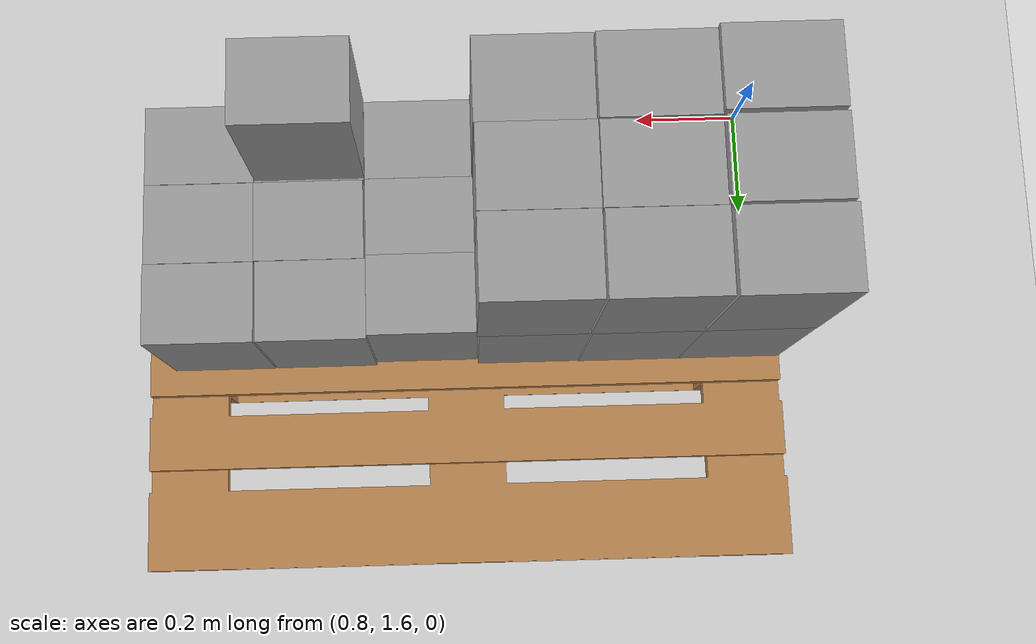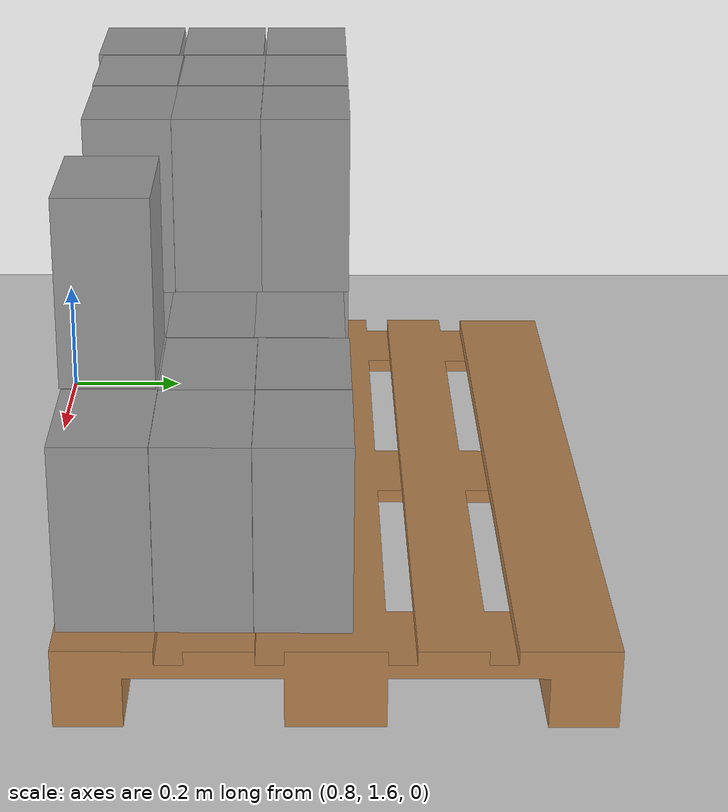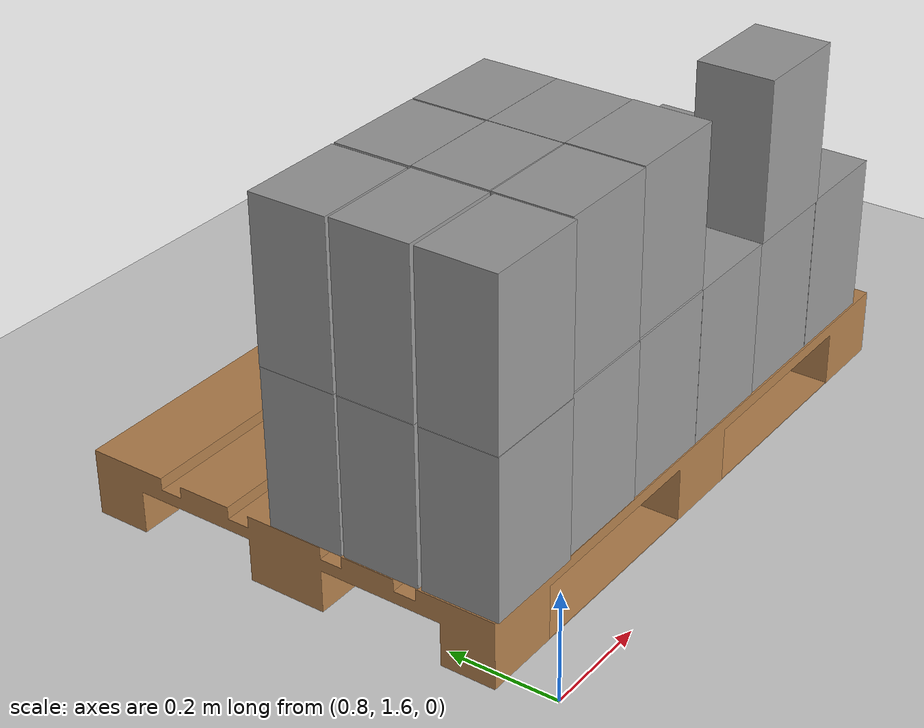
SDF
<sdf version="1.7">
 <world name="default">
  <light name="sun" type="directional">
   <pose>0 0 10 0 -0 0</pose>
   <diffuse>0.8 0.8 0.8 1</diffuse>
   <specular>0.2 0.2 0.2 1</specular>
   <attenuation>
    <range>1000</range>
    <constant>0.9</constant>
    <linear>0.01</linear>
    <quadratic>0.001</quadratic>
   </attenuation>
   <direction>-0.5 0.1 -0.9</direction>
   <spot><inner_angle>0</inner_angle><outer_angle>0</outer_angle><falloff>0</falloff></spot>
  </light>
  <model name="ground_plane">
   <static>1</static>
   <link name="link">
    <collision name="collision">
     <geometry><plane><normal>0 0 1</normal><size>100 100</size></plane></geometry>
     <surface>
      <contact><collide_bitmask>65535</collide_bitmask></contact>
      <friction><ode><mu>100</mu><mu2>50</mu2></ode></friction>
     </surface>
    </collision>
    <visual name="visual">
     <cast_shadows>0</cast_shadows>
     <geometry><plane><normal>0 0 1</normal><size>100 100</size></plane></geometry>
     <material>
      <script><uri>file://media/materials/scripts/gazebo.material</uri><name>Gazebo/Grey</name></script>
     </material>
    </visual>
   </link>
  </model>
  <gravity>0 0 -9.8</gravity>
  <magnetic_field>6e-06 2.3e-05 -4.2e-05</magnetic_field>
  <atmosphere type="adiabatic"/>
  <physics type="ode">
   <max_step_size>0.001</max_step_size>
   <real_time_factor>1</real_time_factor>
   <real_time_update_rate>1000</real_time_update_rate>
  </physics>
  <scene><ambient>0.4 0.4 0.4 1</ambient><background>0.7 0.7 0.7 1</background><shadows>1</shadows></scene>
  <spherical_coordinates>
   <surface_model>EARTH_WGS84</surface_model>
   <latitude_deg>0</latitude_deg>
   <longitude_deg>0</longitude_deg>
   <elevation>0</elevation>
   <heading_deg>0</heading_deg>
  </spherical_coordinates>
  <model name="pedana">
   <link name="base">
    <inertial>
     <mass>25</mass>
     <inertia><ixx>1.36434</ixx><ixy>0</ixy><ixz>0</ixz><iyy>3.03101</iyy><iyz>0</iyz><izz>4.33333</izz></inertia>
    </inertial>
    <self_collide>1</self_collide>
    <visual name="visual">
     <pose>-0.6 -0.4 -0.083 0 -0 0</pose>
     <geometry>
      <mesh><uri>/home/marco/catkin_ws_iliad/src/iliad/meshes/pallet_base.stl</uri><scale>1 1 1</scale></mesh>
     </geometry>
     <material>
      <lighting>1</lighting>
      <script><uri>file://media/materials/scripts/gazebo.material</uri><name>Gazebo/Wood</name></script>
      <shader type="pixel"><normal_map>__default__</normal_map></shader>
      <ambient>0.3 0.3 0.3 1</ambient>
      <diffuse>0.7 0.7 0.7 1</diffuse>
      <specular>0.01 0.01 0.01 1</specular>
      <emissive>0 0 0 1</emissive>
     </material>
    </visual>
    <collision name="collision">
     <geometry><box><size>1.2 0.8 0.122</size></box></geometry>
     <surface>
      <friction>
       <ode><mu>1</mu><mu2>1</mu2><fdir1>0 0 0</fdir1><slip1>0</slip1><slip2>0</slip2></ode>
       <torsional>
        <coefficient>1</coefficient>
        <patch_radius>0</patch_radius>
        <surface_radius>0</surface_radius>
        <use_patch_radius>1</use_patch_radius>
        <ode><slip>0</slip></ode>
       </torsional>
      </friction>
      <bounce><restitution_coefficient>0</restitution_coefficient><threshold>1e+06</threshold></bounce>
      <contact>
       <collide_without_contact>0</collide_without_contact>
       <collide_without_contact_bitmask>1</collide_without_contact_bitmask>
       <collide_bitmask>1</collide_bitmask>
       <ode>
        <soft_cfm>0</soft_cfm>
        <soft_erp>0.2</soft_erp>
        <kp>1e+13</kp>
        <kd>1</kd>
        <max_vel>0.01</max_vel>
        <min_depth>0</min_depth>
       </ode>
       <bullet>
        <split_impulse>1</split_impulse>
        <split_impulse_penetration_threshold>-0.01</split_impulse_penetration_threshold>
        <soft_cfm>0</soft_cfm>
        <soft_erp>0.2</soft_erp>
        <kp>1e+13</kp>
        <kd>1</kd>
       </bullet>
      </contact>
     </surface>
    </collision>
   </link>
   <static>1</static>
   <pose>1.36911 2.09324 0.060991 3e-05 3.5e-05 4.8e-05</pose>
  </model>
  <model name="box_19_14_29">
   <link name="link_0">
    <inertial>
     <mass>3</mass>
     <inertia>
      <ixx>0.025925</ixx>
      <ixy>0</ixy>
      <ixz>0</ixz>
      <iyy>0.03005</iyy>
      <iyz>0</iyz>
      <izz>0.013925</izz>
     </inertia>
    </inertial>
    <visual name="visual">
     <geometry><box><size>0.19 0.14 0.29</size></box></geometry>
     <material>
      <lighting>1</lighting>
      <script><uri>file://media/materials/scripts/gazebo.material</uri><name>Gazebo/Grey</name></script>
      <shader type="pixel"><normal_map>__default__</normal_map></shader>
      <ambient>0.3 0.3 0.3 1</ambient>
      <diffuse>0.7 0.7 0.7 1</diffuse>
      <specular>0.01 0.01 0.01 1</specular>
      <emissive>0 0 0 1</emissive>
     </material>
    </visual>
    <collision name="collision">
     <geometry><box><size>0.19 0.14 0.29</size></box></geometry>
     <surface>
      <friction>
       <ode><mu>0.6</mu><mu2>0.6</mu2><fdir1>0 0 0</fdir1><slip1>0</slip1><slip2>0</slip2></ode>
       <torsional>
        <coefficient>1</coefficient>
        <patch_radius>0</patch_radius>
        <surface_radius>0</surface_radius>
        <use_patch_radius>1</use_patch_radius>
        <ode><slip>0</slip></ode>
       </torsional>
      </friction>
      <bounce><restitution_coefficient>0</restitution_coefficient><threshold>1e+06</threshold></bounce>
      <contact>
       <collide_without_contact>0</collide_without_contact>
       <collide_without_contact_bitmask>1</collide_without_contact_bitmask>
       <collide_bitmask>1</collide_bitmask>
       <ode>
        <soft_cfm>0</soft_cfm>
        <soft_erp>0.2</soft_erp>
        <kp>1e+13</kp>
        <kd>1</kd>
        <max_vel>0.01</max_vel>
        <min_depth>0.01</min_depth>
       </ode>
       <bullet>
        <split_impulse>1</split_impulse>
        <split_impulse_penetration_threshold>-0.01</split_impulse_penetration_threshold>
        <soft_cfm>0</soft_cfm>
        <soft_erp>0.2</soft_erp>
        <kp>1e+13</kp>
        <kd>1</kd>
       </bullet>
      </contact>
     </surface>
    </collision>
   </link>
   <static>0</static>
   <pose>1.63127 1.76389 0.556988 -3.4e-05 2e-05 -0.001481</pose>
  </model>
  <model name="box_19_14_29_0">
   <link name="link_0">
    <inertial>
     <mass>3</mass>
     <inertia>
      <ixx>0.025925</ixx>
      <ixy>0</ixy>
      <ixz>0</ixz>
      <iyy>0.03005</iyy>
      <iyz>0</iyz>
      <izz>0.013925</izz>
     </inertia>
    </inertial>
    <visual name="visual">
     <geometry><box><size>0.19 0.14 0.29</size></box></geometry>
     <material>
      <lighting>1</lighting>
      <script><uri>file://media/materials/scripts/gazebo.material</uri><name>Gazebo/Grey</name></script>
      <shader type="pixel"><normal_map>__default__</normal_map></shader>
      <ambient>0.3 0.3 0.3 1</ambient>
      <diffuse>0.7 0.7 0.7 1</diffuse>
      <specular>0.01 0.01 0.01 1</specular>
      <emissive>0 0 0 1</emissive>
     </material>
    </visual>
    <collision name="collision">
     <geometry><box><size>0.19 0.14 0.29</size></box></geometry>
     <surface>
      <friction>
       <ode><mu>0.6</mu><mu2>0.6</mu2><fdir1>0 0 0</fdir1><slip1>0</slip1><slip2>0</slip2></ode>
       <torsional>
        <coefficient>1</coefficient>
        <patch_radius>0</patch_radius>
        <surface_radius>0</surface_radius>
        <use_patch_radius>1</use_patch_radius>
        <ode><slip>0</slip></ode>
       </torsional>
      </friction>
      <bounce><restitution_coefficient>0</restitution_coefficient><threshold>1e+06</threshold></bounce>
      <contact>
       <collide_without_contact>0</collide_without_contact>
       <collide_without_contact_bitmask>1</collide_without_contact_bitmask>
       <collide_bitmask>1</collide_bitmask>
       <ode>
        <soft_cfm>0</soft_cfm>
        <soft_erp>0.2</soft_erp>
        <kp>1e+13</kp>
        <kd>1</kd>
        <max_vel>0.01</max_vel>
        <min_depth>0.01</min_depth>
       </ode>
       <bullet>
        <split_impulse>1</split_impulse>
        <split_impulse_penetration_threshold>-0.01</split_impulse_penetration_threshold>
        <soft_cfm>0</soft_cfm>
        <soft_erp>0.2</soft_erp>
        <kp>1e+13</kp>
        <kd>1</kd>
       </bullet>
      </contact>
     </surface>
    </collision>
   </link>
   <static>1</static>
   <pose>0.866212 1.90477 0.267012 6.7e-05 0.000116 0.001132</pose>
  </model>
  <model name="box_19_14_29_1">
   <link name="link_0">
    <inertial>
     <mass>3</mass>
     <inertia>
      <ixx>0.025925</ixx>
      <ixy>0</ixy>
      <ixz>0</ixz>
      <iyy>0.03005</iyy>
      <iyz>0</iyz>
      <izz>0.013925</izz>
     </inertia>
    </inertial>
    <visual name="visual">
     <geometry><box><size>0.19 0.14 0.29</size></box></geometry>
     <material>
      <lighting>1</lighting>
      <script><uri>file://media/materials/scripts/gazebo.material</uri><name>Gazebo/Grey</name></script>
      <shader type="pixel"><normal_map>__default__</normal_map></shader>
      <ambient>0.3 0.3 0.3 1</ambient>
      <diffuse>0.7 0.7 0.7 1</diffuse>
      <specular>0.01 0.01 0.01 1</specular>
      <emissive>0 0 0 1</emissive>
     </material>
    </visual>
    <collision name="collision">
     <geometry><box><size>0.19 0.14 0.29</size></box></geometry>
     <surface>
      <friction>
       <ode><mu>0.6</mu><mu2>0.6</mu2><fdir1>0 0 0</fdir1><slip1>0</slip1><slip2>0</slip2></ode>
       <torsional>
        <coefficient>1</coefficient>
        <patch_radius>0</patch_radius>
        <surface_radius>0</surface_radius>
        <use_patch_radius>1</use_patch_radius>
        <ode><slip>0</slip></ode>
       </torsional>
      </friction>
      <bounce><restitution_coefficient>0</restitution_coefficient><threshold>1e+06</threshold></bounce>
      <contact>
       <collide_without_contact>0</collide_without_contact>
       <collide_without_contact_bitmask>1</collide_without_contact_bitmask>
       <collide_bitmask>1</collide_bitmask>
       <ode>
        <soft_cfm>0</soft_cfm>
        <soft_erp>0.2</soft_erp>
        <kp>1e+13</kp>
        <kd>1</kd>
        <max_vel>0.01</max_vel>
        <min_depth>0.01</min_depth>
       </ode>
       <bullet>
        <split_impulse>1</split_impulse>
        <split_impulse_penetration_threshold>-0.01</split_impulse_penetration_threshold>
        <soft_cfm>0</soft_cfm>
        <soft_erp>0.2</soft_erp>
        <kp>1e+13</kp>
        <kd>1</kd>
       </bullet>
      </contact>
     </surface>
    </collision>
   </link>
   <static>1</static>
   <pose>0.865082 2.04928 0.267013 2.6e-05 9.9e-05 0.001315</pose>
  </model>
  <model name="box_19_14_29_2">
   <link name="link_0">
    <inertial>
     <mass>3</mass>
     <inertia>
      <ixx>0.025925</ixx>
      <ixy>0</ixy>
      <ixz>0</ixz>
      <iyy>0.03005</iyy>
      <iyz>0</iyz>
      <izz>0.013925</izz>
     </inertia>
    </inertial>
    <visual name="visual">
     <geometry><box><size>0.19 0.14 0.29</size></box></geometry>
     <material>
      <lighting>1</lighting>
      <script><uri>file://media/materials/scripts/gazebo.material</uri><name>Gazebo/Grey</name></script>
      <shader type="pixel"><normal_map>__default__</normal_map></shader>
      <ambient>0.3 0.3 0.3 1</ambient>
      <diffuse>0.7 0.7 0.7 1</diffuse>
      <specular>0.01 0.01 0.01 1</specular>
      <emissive>0 0 0 1</emissive>
     </material>
    </visual>
    <collision name="collision">
     <geometry><box><size>0.19 0.14 0.29</size></box></geometry>
     <surface>
      <friction>
       <ode><mu>0.6</mu><mu2>0.6</mu2><fdir1>0 0 0</fdir1><slip1>0</slip1><slip2>0</slip2></ode>
       <torsional>
        <coefficient>1</coefficient>
        <patch_radius>0</patch_radius>
        <surface_radius>0</surface_radius>
        <use_patch_radius>1</use_patch_radius>
        <ode><slip>0</slip></ode>
       </torsional>
      </friction>
      <bounce><restitution_coefficient>0</restitution_coefficient><threshold>1e+06</threshold></bounce>
      <contact>
       <collide_without_contact>0</collide_without_contact>
       <collide_without_contact_bitmask>1</collide_without_contact_bitmask>
       <collide_bitmask>1</collide_bitmask>
       <ode>
        <soft_cfm>0</soft_cfm>
        <soft_erp>0.2</soft_erp>
        <kp>1e+13</kp>
        <kd>1</kd>
        <max_vel>0.01</max_vel>
        <min_depth>0.01</min_depth>
       </ode>
       <bullet>
        <split_impulse>1</split_impulse>
        <split_impulse_penetration_threshold>-0.01</split_impulse_penetration_threshold>
        <soft_cfm>0</soft_cfm>
        <soft_erp>0.2</soft_erp>
        <kp>1e+13</kp>
        <kd>1</kd>
       </bullet>
      </contact>
     </surface>
    </collision>
   </link>
   <static>1</static>
   <pose>1.05734 2.04939 0.26698 5e-06 -3.3e-05 0.00024</pose>
  </model>
  <model name="box_19_14_29_3">
   <link name="link_0">
    <inertial>
     <mass>3</mass>
     <inertia>
      <ixx>0.025925</ixx>
      <ixy>0</ixy>
      <ixz>0</ixz>
      <iyy>0.03005</iyy>
      <iyz>0</iyz>
      <izz>0.013925</izz>
     </inertia>
    </inertial>
    <visual name="visual">
     <geometry><box><size>0.19 0.14 0.29</size></box></geometry>
     <material>
      <lighting>1</lighting>
      <script><uri>file://media/materials/scripts/gazebo.material</uri><name>Gazebo/Grey</name></script>
      <shader type="pixel"><normal_map>__default__</normal_map></shader>
      <ambient>0.3 0.3 0.3 1</ambient>
      <diffuse>0.7 0.7 0.7 1</diffuse>
      <specular>0.01 0.01 0.01 1</specular>
      <emissive>0 0 0 1</emissive>
     </material>
    </visual>
    <collision name="collision">
     <geometry><box><size>0.19 0.14 0.29</size></box></geometry>
     <surface>
      <friction>
       <ode><mu>0.6</mu><mu2>0.6</mu2><fdir1>0 0 0</fdir1><slip1>0</slip1><slip2>0</slip2></ode>
       <torsional>
        <coefficient>1</coefficient>
        <patch_radius>0</patch_radius>
        <surface_radius>0</surface_radius>
        <use_patch_radius>1</use_patch_radius>
        <ode><slip>0</slip></ode>
       </torsional>
      </friction>
      <bounce><restitution_coefficient>0</restitution_coefficient><threshold>1e+06</threshold></bounce>
      <contact>
       <collide_without_contact>0</collide_without_contact>
       <collide_without_contact_bitmask>1</collide_without_contact_bitmask>
       <collide_bitmask>1</collide_bitmask>
       <ode>
        <soft_cfm>0</soft_cfm>
        <soft_erp>0.2</soft_erp>
        <kp>1e+13</kp>
        <kd>1</kd>
        <max_vel>0.01</max_vel>
        <min_depth>0.01</min_depth>
       </ode>
       <bullet>
        <split_impulse>1</split_impulse>
        <split_impulse_penetration_threshold>-0.01</split_impulse_penetration_threshold>
        <soft_cfm>0</soft_cfm>
        <soft_erp>0.2</soft_erp>
        <kp>1e+13</kp>
        <kd>1</kd>
       </bullet>
      </contact>
     </surface>
    </collision>
   </link>
   <static>1</static>
   <pose>1.06057 1.90593 0.26698 -7e-06 1.4e-05 -0.000942</pose>
  </model>
  <model name="box_19_14_29_4">
   <link name="link_0">
    <inertial>
     <mass>3</mass>
     <inertia>
      <ixx>0.025925</ixx>
      <ixy>0</ixy>
      <ixz>0</ixz>
      <iyy>0.03005</iyy>
      <iyz>0</iyz>
      <izz>0.013925</izz>
     </inertia>
    </inertial>
    <visual name="visual">
     <geometry><box><size>0.19 0.14 0.29</size></box></geometry>
     <material>
      <lighting>1</lighting>
      <script><uri>file://media/materials/scripts/gazebo.material</uri><name>Gazebo/Grey</name></script>
      <shader type="pixel"><normal_map>__default__</normal_map></shader>
      <ambient>0.3 0.3 0.3 1</ambient>
      <diffuse>0.7 0.7 0.7 1</diffuse>
      <specular>0.01 0.01 0.01 1</specular>
      <emissive>0 0 0 1</emissive>
     </material>
    </visual>
    <collision name="collision">
     <geometry><box><size>0.19 0.14 0.29</size></box></geometry>
     <surface>
      <friction>
       <ode><mu>0.6</mu><mu2>0.6</mu2><fdir1>0 0 0</fdir1><slip1>0</slip1><slip2>0</slip2></ode>
       <torsional>
        <coefficient>1</coefficient>
        <patch_radius>0</patch_radius>
        <surface_radius>0</surface_radius>
        <use_patch_radius>1</use_patch_radius>
        <ode><slip>0</slip></ode>
       </torsional>
      </friction>
      <bounce><restitution_coefficient>0</restitution_coefficient><threshold>1e+06</threshold></bounce>
      <contact>
       <collide_without_contact>0</collide_without_contact>
       <collide_without_contact_bitmask>1</collide_without_contact_bitmask>
       <collide_bitmask>1</collide_bitmask>
       <ode>
        <soft_cfm>0</soft_cfm>
        <soft_erp>0.2</soft_erp>
        <kp>1e+13</kp>
        <kd>1</kd>
        <max_vel>0.01</max_vel>
        <min_depth>0.01</min_depth>
       </ode>
       <bullet>
        <split_impulse>1</split_impulse>
        <split_impulse_penetration_threshold>-0.01</split_impulse_penetration_threshold>
        <soft_cfm>0</soft_cfm>
        <soft_erp>0.2</soft_erp>
        <kp>1e+13</kp>
        <kd>1</kd>
       </bullet>
      </contact>
     </surface>
    </collision>
   </link>
   <static>1</static>
   <pose>1.05936 1.76411 0.266976 3.5e-05 -0.000135 -0.001245</pose>
  </model>
  <model name="box_19_14_29_5">
   <link name="link_0">
    <inertial>
     <mass>3</mass>
     <inertia>
      <ixx>0.025925</ixx>
      <ixy>0</ixy>
      <ixz>0</ixz>
      <iyy>0.03005</iyy>
      <iyz>0</iyz>
      <izz>0.013925</izz>
     </inertia>
    </inertial>
    <visual name="visual">
     <geometry><box><size>0.19 0.14 0.29</size></box></geometry>
     <material>
      <lighting>1</lighting>
      <script><uri>file://media/materials/scripts/gazebo.material</uri><name>Gazebo/Grey</name></script>
      <shader type="pixel"><normal_map>__default__</normal_map></shader>
      <ambient>0.3 0.3 0.3 1</ambient>
      <diffuse>0.7 0.7 0.7 1</diffuse>
      <specular>0.01 0.01 0.01 1</specular>
      <emissive>0 0 0 1</emissive>
     </material>
    </visual>
    <collision name="collision">
     <geometry><box><size>0.19 0.14 0.29</size></box></geometry>
     <surface>
      <friction>
       <ode><mu>0.6</mu><mu2>0.6</mu2><fdir1>0 0 0</fdir1><slip1>0</slip1><slip2>0</slip2></ode>
       <torsional>
        <coefficient>1</coefficient>
        <patch_radius>0</patch_radius>
        <surface_radius>0</surface_radius>
        <use_patch_radius>1</use_patch_radius>
        <ode><slip>0</slip></ode>
       </torsional>
      </friction>
      <bounce><restitution_coefficient>0</restitution_coefficient><threshold>1e+06</threshold></bounce>
      <contact>
       <collide_without_contact>0</collide_without_contact>
       <collide_without_contact_bitmask>1</collide_without_contact_bitmask>
       <collide_bitmask>1</collide_bitmask>
       <ode>
        <soft_cfm>0</soft_cfm>
        <soft_erp>0.2</soft_erp>
        <kp>1e+13</kp>
        <kd>1</kd>
        <max_vel>0.01</max_vel>
        <min_depth>0.01</min_depth>
       </ode>
       <bullet>
        <split_impulse>1</split_impulse>
        <split_impulse_penetration_threshold>-0.01</split_impulse_penetration_threshold>
        <soft_cfm>0</soft_cfm>
        <soft_erp>0.2</soft_erp>
        <kp>1e+13</kp>
        <kd>1</kd>
       </bullet>
      </contact>
     </surface>
    </collision>
   </link>
   <static>1</static>
   <pose>1.25022 1.76566 0.266976 0.000153 -0.000155 -0.001401</pose>
  </model>
  <model name="box_19_14_29_6">
   <link name="link_0">
    <inertial>
     <mass>3</mass>
     <inertia>
      <ixx>0.025925</ixx>
      <ixy>0</ixy>
      <ixz>0</ixz>
      <iyy>0.03005</iyy>
      <iyz>0</iyz>
      <izz>0.013925</izz>
     </inertia>
    </inertial>
    <visual name="visual">
     <geometry><box><size>0.19 0.14 0.29</size></box></geometry>
     <material>
      <lighting>1</lighting>
      <script><uri>file://media/materials/scripts/gazebo.material</uri><name>Gazebo/Grey</name></script>
      <shader type="pixel"><normal_map>__default__</normal_map></shader>
      <ambient>0.3 0.3 0.3 1</ambient>
      <diffuse>0.7 0.7 0.7 1</diffuse>
      <specular>0.01 0.01 0.01 1</specular>
      <emissive>0 0 0 1</emissive>
     </material>
    </visual>
    <collision name="collision">
     <geometry><box><size>0.19 0.14 0.29</size></box></geometry>
     <surface>
      <friction>
       <ode><mu>0.6</mu><mu2>0.6</mu2><fdir1>0 0 0</fdir1><slip1>0</slip1><slip2>0</slip2></ode>
       <torsional>
        <coefficient>1</coefficient>
        <patch_radius>0</patch_radius>
        <surface_radius>0</surface_radius>
        <use_patch_radius>1</use_patch_radius>
        <ode><slip>0</slip></ode>
       </torsional>
      </friction>
      <bounce><restitution_coefficient>0</restitution_coefficient><threshold>1e+06</threshold></bounce>
      <contact>
       <collide_without_contact>0</collide_without_contact>
       <collide_without_contact_bitmask>1</collide_without_contact_bitmask>
       <collide_bitmask>1</collide_bitmask>
       <ode>
        <soft_cfm>0</soft_cfm>
        <soft_erp>0.2</soft_erp>
        <kp>1e+13</kp>
        <kd>1</kd>
        <max_vel>0.01</max_vel>
        <min_depth>0.01</min_depth>
       </ode>
       <bullet>
        <split_impulse>1</split_impulse>
        <split_impulse_penetration_threshold>-0.01</split_impulse_penetration_threshold>
        <soft_cfm>0</soft_cfm>
        <soft_erp>0.2</soft_erp>
        <kp>1e+13</kp>
        <kd>1</kd>
       </bullet>
      </contact>
     </surface>
    </collision>
   </link>
   <static>1</static>
   <pose>1.44105 1.7658 0.267001 0.000567 -0.000129 5.7e-05</pose>
  </model>
  <model name="box_19_14_29_7">
   <link name="link_0">
    <inertial>
     <mass>3</mass>
     <inertia>
      <ixx>0.025925</ixx>
      <ixy>0</ixy>
      <ixz>0</ixz>
      <iyy>0.03005</iyy>
      <iyz>0</iyz>
      <izz>0.013925</izz>
     </inertia>
    </inertial>
    <visual name="visual">
     <geometry><box><size>0.19 0.14 0.29</size></box></geometry>
     <material>
      <lighting>1</lighting>
      <script><uri>file://media/materials/scripts/gazebo.material</uri><name>Gazebo/Grey</name></script>
      <shader type="pixel"><normal_map>__default__</normal_map></shader>
      <ambient>0.3 0.3 0.3 1</ambient>
      <diffuse>0.7 0.7 0.7 1</diffuse>
      <specular>0.01 0.01 0.01 1</specular>
      <emissive>0 0 0 1</emissive>
     </material>
    </visual>
    <collision name="collision">
     <geometry><box><size>0.19 0.14 0.29</size></box></geometry>
     <surface>
      <friction>
       <ode><mu>0.6</mu><mu2>0.6</mu2><fdir1>0 0 0</fdir1><slip1>0</slip1><slip2>0</slip2></ode>
       <torsional>
        <coefficient>1</coefficient>
        <patch_radius>0</patch_radius>
        <surface_radius>0</surface_radius>
        <use_patch_radius>1</use_patch_radius>
        <ode><slip>0</slip></ode>
       </torsional>
      </friction>
      <bounce><restitution_coefficient>0</restitution_coefficient><threshold>1e+06</threshold></bounce>
      <contact>
       <collide_without_contact>0</collide_without_contact>
       <collide_without_contact_bitmask>1</collide_without_contact_bitmask>
       <collide_bitmask>1</collide_bitmask>
       <ode>
        <soft_cfm>0</soft_cfm>
        <soft_erp>0.2</soft_erp>
        <kp>1e+13</kp>
        <kd>1</kd>
        <max_vel>0.01</max_vel>
        <min_depth>0.01</min_depth>
       </ode>
       <bullet>
        <split_impulse>1</split_impulse>
        <split_impulse_penetration_threshold>-0.01</split_impulse_penetration_threshold>
        <soft_cfm>0</soft_cfm>
        <soft_erp>0.2</soft_erp>
        <kp>1e+13</kp>
        <kd>1</kd>
       </bullet>
      </contact>
     </surface>
    </collision>
   </link>
   <static>1</static>
   <pose>1.63192 1.76669 0.266996 3.4e-05 2.3e-05 -0.000499</pose>
  </model>
  <model name="box_19_14_29_8">
   <link name="link_0">
    <inertial>
     <mass>3</mass>
     <inertia>
      <ixx>0.025925</ixx>
      <ixy>0</ixy>
      <ixz>0</ixz>
      <iyy>0.03005</iyy>
      <iyz>0</iyz>
      <izz>0.013925</izz>
     </inertia>
    </inertial>
    <visual name="visual">
     <geometry><box><size>0.19 0.14 0.29</size></box></geometry>
     <material>
      <lighting>1</lighting>
      <script><uri>file://media/materials/scripts/gazebo.material</uri><name>Gazebo/Grey</name></script>
      <shader type="pixel"><normal_map>__default__</normal_map></shader>
      <ambient>0.3 0.3 0.3 1</ambient>
      <diffuse>0.7 0.7 0.7 1</diffuse>
      <specular>0.01 0.01 0.01 1</specular>
      <emissive>0 0 0 1</emissive>
     </material>
    </visual>
    <collision name="collision">
     <geometry><box><size>0.19 0.14 0.29</size></box></geometry>
     <surface>
      <friction>
       <ode><mu>0.6</mu><mu2>0.6</mu2><fdir1>0 0 0</fdir1><slip1>0</slip1><slip2>0</slip2></ode>
       <torsional>
        <coefficient>1</coefficient>
        <patch_radius>0</patch_radius>
        <surface_radius>0</surface_radius>
        <use_patch_radius>1</use_patch_radius>
        <ode><slip>0</slip></ode>
       </torsional>
      </friction>
      <bounce><restitution_coefficient>0</restitution_coefficient><threshold>1e+06</threshold></bounce>
      <contact>
       <collide_without_contact>0</collide_without_contact>
       <collide_without_contact_bitmask>1</collide_without_contact_bitmask>
       <collide_bitmask>1</collide_bitmask>
       <ode>
        <soft_cfm>0</soft_cfm>
        <soft_erp>0.2</soft_erp>
        <kp>1e+13</kp>
        <kd>1</kd>
        <max_vel>0.01</max_vel>
        <min_depth>0.01</min_depth>
       </ode>
       <bullet>
        <split_impulse>1</split_impulse>
        <split_impulse_penetration_threshold>-0.01</split_impulse_penetration_threshold>
        <soft_cfm>0</soft_cfm>
        <soft_erp>0.2</soft_erp>
        <kp>1e+13</kp>
        <kd>1</kd>
       </bullet>
      </contact>
     </surface>
    </collision>
   </link>
   <static>1</static>
   <pose>1.82298 1.76663 0.266992 -1.1e-05 -0.000144 -0.000473</pose>
  </model>
  <model name="box_19_14_29_9">
   <link name="link_0">
    <inertial>
     <mass>3</mass>
     <inertia>
      <ixx>0.025925</ixx>
      <ixy>0</ixy>
      <ixz>0</ixz>
      <iyy>0.03005</iyy>
      <iyz>0</iyz>
      <izz>0.013925</izz>
     </inertia>
    </inertial>
    <visual name="visual">
     <geometry><box><size>0.19 0.14 0.29</size></box></geometry>
     <material>
      <lighting>1</lighting>
      <script><uri>file://media/materials/scripts/gazebo.material</uri><name>Gazebo/Grey</name></script>
      <shader type="pixel"><normal_map>__default__</normal_map></shader>
      <ambient>0.3 0.3 0.3 1</ambient>
      <diffuse>0.7 0.7 0.7 1</diffuse>
      <specular>0.01 0.01 0.01 1</specular>
      <emissive>0 0 0 1</emissive>
     </material>
    </visual>
    <collision name="collision">
     <geometry><box><size>0.19 0.14 0.29</size></box></geometry>
     <surface>
      <friction>
       <ode><mu>0.6</mu><mu2>0.6</mu2><fdir1>0 0 0</fdir1><slip1>0</slip1><slip2>0</slip2></ode>
       <torsional>
        <coefficient>1</coefficient>
        <patch_radius>0</patch_radius>
        <surface_radius>0</surface_radius>
        <use_patch_radius>1</use_patch_radius>
        <ode><slip>0</slip></ode>
       </torsional>
      </friction>
      <bounce><restitution_coefficient>0</restitution_coefficient><threshold>1e+06</threshold></bounce>
      <contact>
       <collide_without_contact>0</collide_without_contact>
       <collide_without_contact_bitmask>1</collide_without_contact_bitmask>
       <collide_bitmask>1</collide_bitmask>
       <ode>
        <soft_cfm>0</soft_cfm>
        <soft_erp>0.2</soft_erp>
        <kp>1e+13</kp>
        <kd>1</kd>
        <max_vel>0.01</max_vel>
        <min_depth>0.01</min_depth>
       </ode>
       <bullet>
        <split_impulse>1</split_impulse>
        <split_impulse_penetration_threshold>-0.01</split_impulse_penetration_threshold>
        <soft_cfm>0</soft_cfm>
        <soft_erp>0.2</soft_erp>
        <kp>1e+13</kp>
        <kd>1</kd>
       </bullet>
      </contact>
     </surface>
    </collision>
   </link>
   <static>1</static>
   <pose>1.25074 1.90578 0.266992 0.000149 -8.1e-05 -0.00253</pose>
  </model>
  <model name="box_19_14_29_10">
   <link name="link_0">
    <inertial>
     <mass>3</mass>
     <inertia>
      <ixx>0.025925</ixx>
      <ixy>0</ixy>
      <ixz>0</ixz>
      <iyy>0.03005</iyy>
      <iyz>0</iyz>
      <izz>0.013925</izz>
     </inertia>
    </inertial>
    <visual name="visual">
     <geometry><box><size>0.19 0.14 0.29</size></box></geometry>
     <material>
      <lighting>1</lighting>
      <script><uri>file://media/materials/scripts/gazebo.material</uri><name>Gazebo/Grey</name></script>
      <shader type="pixel"><normal_map>__default__</normal_map></shader>
      <ambient>0.3 0.3 0.3 1</ambient>
      <diffuse>0.7 0.7 0.7 1</diffuse>
      <specular>0.01 0.01 0.01 1</specular>
      <emissive>0 0 0 1</emissive>
     </material>
    </visual>
    <collision name="collision">
     <geometry><box><size>0.19 0.14 0.29</size></box></geometry>
     <surface>
      <friction>
       <ode><mu>0.6</mu><mu2>0.6</mu2><fdir1>0 0 0</fdir1><slip1>0</slip1><slip2>0</slip2></ode>
       <torsional>
        <coefficient>1</coefficient>
        <patch_radius>0</patch_radius>
        <surface_radius>0</surface_radius>
        <use_patch_radius>1</use_patch_radius>
        <ode><slip>0</slip></ode>
       </torsional>
      </friction>
      <bounce><restitution_coefficient>0</restitution_coefficient><threshold>1e+06</threshold></bounce>
      <contact>
       <collide_without_contact>0</collide_without_contact>
       <collide_without_contact_bitmask>1</collide_without_contact_bitmask>
       <collide_bitmask>1</collide_bitmask>
       <ode>
        <soft_cfm>0</soft_cfm>
        <soft_erp>0.2</soft_erp>
        <kp>1e+13</kp>
        <kd>1</kd>
        <max_vel>0.01</max_vel>
        <min_depth>0.01</min_depth>
       </ode>
       <bullet>
        <split_impulse>1</split_impulse>
        <split_impulse_penetration_threshold>-0.01</split_impulse_penetration_threshold>
        <soft_cfm>0</soft_cfm>
        <soft_erp>0.2</soft_erp>
        <kp>1e+13</kp>
        <kd>1</kd>
       </bullet>
      </contact>
     </surface>
    </collision>
   </link>
   <static>1</static>
   <pose>1.44149 1.9058 0.267022 0.000596 -0.000104 1e-06</pose>
  </model>
  <model name="box_19_14_29_11">
   <link name="link_0">
    <inertial>
     <mass>3</mass>
     <inertia>
      <ixx>0.025925</ixx>
      <ixy>0</ixy>
      <ixz>0</ixz>
      <iyy>0.03005</iyy>
      <iyz>0</iyz>
      <izz>0.013925</izz>
     </inertia>
    </inertial>
    <visual name="visual">
     <geometry><box><size>0.19 0.14 0.29</size></box></geometry>
     <material>
      <lighting>1</lighting>
      <script><uri>file://media/materials/scripts/gazebo.material</uri><name>Gazebo/Grey</name></script>
      <shader type="pixel"><normal_map>__default__</normal_map></shader>
      <ambient>0.3 0.3 0.3 1</ambient>
      <diffuse>0.7 0.7 0.7 1</diffuse>
      <specular>0.01 0.01 0.01 1</specular>
      <emissive>0 0 0 1</emissive>
     </material>
    </visual>
    <collision name="collision">
     <geometry><box><size>0.19 0.14 0.29</size></box></geometry>
     <surface>
      <friction>
       <ode><mu>0.6</mu><mu2>0.6</mu2><fdir1>0 0 0</fdir1><slip1>0</slip1><slip2>0</slip2></ode>
       <torsional>
        <coefficient>1</coefficient>
        <patch_radius>0</patch_radius>
        <surface_radius>0</surface_radius>
        <use_patch_radius>1</use_patch_radius>
        <ode><slip>0</slip></ode>
       </torsional>
      </friction>
      <bounce><restitution_coefficient>0</restitution_coefficient><threshold>1e+06</threshold></bounce>
      <contact>
       <collide_without_contact>0</collide_without_contact>
       <collide_without_contact_bitmask>1</collide_without_contact_bitmask>
       <collide_bitmask>1</collide_bitmask>
       <ode>
        <soft_cfm>0</soft_cfm>
        <soft_erp>0.2</soft_erp>
        <kp>1e+13</kp>
        <kd>1</kd>
        <max_vel>0.01</max_vel>
        <min_depth>0.01</min_depth>
       </ode>
       <bullet>
        <split_impulse>1</split_impulse>
        <split_impulse_penetration_threshold>-0.01</split_impulse_penetration_threshold>
        <soft_cfm>0</soft_cfm>
        <soft_erp>0.2</soft_erp>
        <kp>1e+13</kp>
        <kd>1</kd>
       </bullet>
      </contact>
     </surface>
    </collision>
   </link>
   <static>1</static>
   <pose>1.63426 1.90673 0.267021 3e-06 -0.000266 -0.000446</pose>
  </model>
  <model name="box_19_14_29_12">
   <link name="link_0">
    <inertial>
     <mass>3</mass>
     <inertia>
      <ixx>0.025925</ixx>
      <ixy>0</ixy>
      <ixz>0</ixz>
      <iyy>0.03005</iyy>
      <iyz>0</iyz>
      <izz>0.013925</izz>
     </inertia>
    </inertial>
    <visual name="visual">
     <geometry><box><size>0.19 0.14 0.29</size></box></geometry>
     <material>
      <lighting>1</lighting>
      <script><uri>file://media/materials/scripts/gazebo.material</uri><name>Gazebo/Grey</name></script>
      <shader type="pixel"><normal_map>__default__</normal_map></shader>
      <ambient>0.3 0.3 0.3 1</ambient>
      <diffuse>0.7 0.7 0.7 1</diffuse>
      <specular>0.01 0.01 0.01 1</specular>
      <emissive>0 0 0 1</emissive>
     </material>
    </visual>
    <collision name="collision">
     <geometry><box><size>0.19 0.14 0.29</size></box></geometry>
     <surface>
      <friction>
       <ode><mu>0.6</mu><mu2>0.6</mu2><fdir1>0 0 0</fdir1><slip1>0</slip1><slip2>0</slip2></ode>
       <torsional>
        <coefficient>1</coefficient>
        <patch_radius>0</patch_radius>
        <surface_radius>0</surface_radius>
        <use_patch_radius>1</use_patch_radius>
        <ode><slip>0</slip></ode>
       </torsional>
      </friction>
      <bounce><restitution_coefficient>0</restitution_coefficient><threshold>1e+06</threshold></bounce>
      <contact>
       <collide_without_contact>0</collide_without_contact>
       <collide_without_contact_bitmask>1</collide_without_contact_bitmask>
       <collide_bitmask>1</collide_bitmask>
       <ode>
        <soft_cfm>0</soft_cfm>
        <soft_erp>0.2</soft_erp>
        <kp>1e+13</kp>
        <kd>1</kd>
        <max_vel>0.01</max_vel>
        <min_depth>0.01</min_depth>
       </ode>
       <bullet>
        <split_impulse>1</split_impulse>
        <split_impulse_penetration_threshold>-0.01</split_impulse_penetration_threshold>
        <soft_cfm>0</soft_cfm>
        <soft_erp>0.2</soft_erp>
        <kp>1e+13</kp>
        <kd>1</kd>
       </bullet>
      </contact>
     </surface>
    </collision>
   </link>
   <static>1</static>
   <pose>1.82353 1.90704 0.267011 -4.8e-05 7.3e-05 -0.000626</pose>
  </model>
  <model name="box_19_14_29_13">
   <link name="link_0">
    <inertial>
     <mass>3</mass>
     <inertia>
      <ixx>0.025925</ixx>
      <ixy>0</ixy>
      <ixz>0</ixz>
      <iyy>0.03005</iyy>
      <iyz>0</iyz>
      <izz>0.013925</izz>
     </inertia>
    </inertial>
    <visual name="visual">
     <geometry><box><size>0.19 0.14 0.29</size></box></geometry>
     <material>
      <lighting>1</lighting>
      <script><uri>file://media/materials/scripts/gazebo.material</uri><name>Gazebo/Grey</name></script>
      <shader type="pixel"><normal_map>__default__</normal_map></shader>
      <ambient>0.3 0.3 0.3 1</ambient>
      <diffuse>0.7 0.7 0.7 1</diffuse>
      <specular>0.01 0.01 0.01 1</specular>
      <emissive>0 0 0 1</emissive>
     </material>
    </visual>
    <collision name="collision">
     <geometry><box><size>0.19 0.14 0.29</size></box></geometry>
     <surface>
      <friction>
       <ode><mu>0.6</mu><mu2>0.6</mu2><fdir1>0 0 0</fdir1><slip1>0</slip1><slip2>0</slip2></ode>
       <torsional>
        <coefficient>1</coefficient>
        <patch_radius>0</patch_radius>
        <surface_radius>0</surface_radius>
        <use_patch_radius>1</use_patch_radius>
        <ode><slip>0</slip></ode>
       </torsional>
      </friction>
      <bounce><restitution_coefficient>0</restitution_coefficient><threshold>1e+06</threshold></bounce>
      <contact>
       <collide_without_contact>0</collide_without_contact>
       <collide_without_contact_bitmask>1</collide_without_contact_bitmask>
       <collide_bitmask>1</collide_bitmask>
       <ode>
        <soft_cfm>0</soft_cfm>
        <soft_erp>0.2</soft_erp>
        <kp>1e+13</kp>
        <kd>1</kd>
        <max_vel>0.01</max_vel>
        <min_depth>0.01</min_depth>
       </ode>
       <bullet>
        <split_impulse>1</split_impulse>
        <split_impulse_penetration_threshold>-0.01</split_impulse_penetration_threshold>
        <soft_cfm>0</soft_cfm>
        <soft_erp>0.2</soft_erp>
        <kp>1e+13</kp>
        <kd>1</kd>
       </bullet>
      </contact>
     </surface>
    </collision>
   </link>
   <static>1</static>
   <pose>1.24969 2.04865 0.266995 -4.6e-05 -7.9e-05 0.0005</pose>
  </model>
  <model name="box_19_14_29_14">
   <link name="link_0">
    <inertial>
     <mass>3</mass>
     <inertia>
      <ixx>0.025925</ixx>
      <ixy>0</ixy>
      <ixz>0</ixz>
      <iyy>0.03005</iyy>
      <iyz>0</iyz>
      <izz>0.013925</izz>
     </inertia>
    </inertial>
    <visual name="visual">
     <geometry><box><size>0.19 0.14 0.29</size></box></geometry>
     <material>
      <lighting>1</lighting>
      <script><uri>file://media/materials/scripts/gazebo.material</uri><name>Gazebo/Grey</name></script>
      <shader type="pixel"><normal_map>__default__</normal_map></shader>
      <ambient>0.3 0.3 0.3 1</ambient>
      <diffuse>0.7 0.7 0.7 1</diffuse>
      <specular>0.01 0.01 0.01 1</specular>
      <emissive>0 0 0 1</emissive>
     </material>
    </visual>
    <collision name="collision">
     <geometry><box><size>0.19 0.14 0.29</size></box></geometry>
     <surface>
      <friction>
       <ode><mu>0.6</mu><mu2>0.6</mu2><fdir1>0 0 0</fdir1><slip1>0</slip1><slip2>0</slip2></ode>
       <torsional>
        <coefficient>1</coefficient>
        <patch_radius>0</patch_radius>
        <surface_radius>0</surface_radius>
        <use_patch_radius>1</use_patch_radius>
        <ode><slip>0</slip></ode>
       </torsional>
      </friction>
      <bounce><restitution_coefficient>0</restitution_coefficient><threshold>1e+06</threshold></bounce>
      <contact>
       <collide_without_contact>0</collide_without_contact>
       <collide_without_contact_bitmask>1</collide_without_contact_bitmask>
       <collide_bitmask>1</collide_bitmask>
       <ode>
        <soft_cfm>0</soft_cfm>
        <soft_erp>0.2</soft_erp>
        <kp>1e+13</kp>
        <kd>1</kd>
        <max_vel>0.01</max_vel>
        <min_depth>0.01</min_depth>
       </ode>
       <bullet>
        <split_impulse>1</split_impulse>
        <split_impulse_penetration_threshold>-0.01</split_impulse_penetration_threshold>
        <soft_cfm>0</soft_cfm>
        <soft_erp>0.2</soft_erp>
        <kp>1e+13</kp>
        <kd>1</kd>
       </bullet>
      </contact>
     </surface>
    </collision>
   </link>
   <static>1</static>
   <pose>1.44218 2.04068 0.267112 -0.001522 -9.8e-05 0.000664</pose>
  </model>
  <model name="box_19_14_29_15">
   <link name="link_0">
    <inertial>
     <mass>3</mass>
     <inertia>
      <ixx>0.025925</ixx>
      <ixy>0</ixy>
      <ixz>0</ixz>
      <iyy>0.03005</iyy>
      <iyz>0</iyz>
      <izz>0.013925</izz>
     </inertia>
    </inertial>
    <visual name="visual">
     <geometry><box><size>0.19 0.14 0.29</size></box></geometry>
     <material>
      <lighting>1</lighting>
      <script><uri>file://media/materials/scripts/gazebo.material</uri><name>Gazebo/Grey</name></script>
      <shader type="pixel"><normal_map>__default__</normal_map></shader>
      <ambient>0.3 0.3 0.3 1</ambient>
      <diffuse>0.7 0.7 0.7 1</diffuse>
      <specular>0.01 0.01 0.01 1</specular>
      <emissive>0 0 0 1</emissive>
     </material>
    </visual>
    <collision name="collision">
     <geometry><box><size>0.19 0.14 0.29</size></box></geometry>
     <surface>
      <friction>
       <ode><mu>0.6</mu><mu2>0.6</mu2><fdir1>0 0 0</fdir1><slip1>0</slip1><slip2>0</slip2></ode>
       <torsional>
        <coefficient>1</coefficient>
        <patch_radius>0</patch_radius>
        <surface_radius>0</surface_radius>
        <use_patch_radius>1</use_patch_radius>
        <ode><slip>0</slip></ode>
       </torsional>
      </friction>
      <bounce><restitution_coefficient>0</restitution_coefficient><threshold>1e+06</threshold></bounce>
      <contact>
       <collide_without_contact>0</collide_without_contact>
       <collide_without_contact_bitmask>1</collide_without_contact_bitmask>
       <collide_bitmask>1</collide_bitmask>
       <ode>
        <soft_cfm>0</soft_cfm>
        <soft_erp>0.2</soft_erp>
        <kp>1e+13</kp>
        <kd>1</kd>
        <max_vel>0.01</max_vel>
        <min_depth>0.01</min_depth>
       </ode>
       <bullet>
        <split_impulse>1</split_impulse>
        <split_impulse_penetration_threshold>-0.01</split_impulse_penetration_threshold>
        <soft_cfm>0</soft_cfm>
        <soft_erp>0.2</soft_erp>
        <kp>1e+13</kp>
        <kd>1</kd>
       </bullet>
      </contact>
     </surface>
    </collision>
   </link>
   <static>1</static>
   <pose>1.6322 2.04704 0.266999 -9.9e-05 -6.2e-05 0.000618</pose>
  </model>
  <model name="box_19_14_29_16">
   <link name="link_0">
    <inertial>
     <mass>3</mass>
     <inertia>
      <ixx>0.025925</ixx>
      <ixy>0</ixy>
      <ixz>0</ixz>
      <iyy>0.03005</iyy>
      <iyz>0</iyz>
      <izz>0.013925</izz>
     </inertia>
    </inertial>
    <visual name="visual">
     <geometry><box><size>0.19 0.14 0.29</size></box></geometry>
     <material>
      <lighting>1</lighting>
      <script><uri>file://media/materials/scripts/gazebo.material</uri><name>Gazebo/Grey</name></script>
      <shader type="pixel"><normal_map>__default__</normal_map></shader>
      <ambient>0.3 0.3 0.3 1</ambient>
      <diffuse>0.7 0.7 0.7 1</diffuse>
      <specular>0.01 0.01 0.01 1</specular>
      <emissive>0 0 0 1</emissive>
     </material>
    </visual>
    <collision name="collision">
     <geometry><box><size>0.19 0.14 0.29</size></box></geometry>
     <surface>
      <friction>
       <ode><mu>0.6</mu><mu2>0.6</mu2><fdir1>0 0 0</fdir1><slip1>0</slip1><slip2>0</slip2></ode>
       <torsional>
        <coefficient>1</coefficient>
        <patch_radius>0</patch_radius>
        <surface_radius>0</surface_radius>
        <use_patch_radius>1</use_patch_radius>
        <ode><slip>0</slip></ode>
       </torsional>
      </friction>
      <bounce><restitution_coefficient>0</restitution_coefficient><threshold>1e+06</threshold></bounce>
      <contact>
       <collide_without_contact>0</collide_without_contact>
       <collide_without_contact_bitmask>1</collide_without_contact_bitmask>
       <collide_bitmask>1</collide_bitmask>
       <ode>
        <soft_cfm>0</soft_cfm>
        <soft_erp>0.2</soft_erp>
        <kp>1e+13</kp>
        <kd>1</kd>
        <max_vel>0.01</max_vel>
        <min_depth>0.01</min_depth>
       </ode>
       <bullet>
        <split_impulse>1</split_impulse>
        <split_impulse_penetration_threshold>-0.01</split_impulse_penetration_threshold>
        <soft_cfm>0</soft_cfm>
        <soft_erp>0.2</soft_erp>
        <kp>1e+13</kp>
        <kd>1</kd>
       </bullet>
      </contact>
     </surface>
    </collision>
   </link>
   <static>1</static>
   <pose>1.82482 2.04744 0.267008 9e-06 3e-06 -0.001067</pose>
  </model>
  <model name="box_19_14_29_17">
   <link name="link_0">
    <inertial>
     <mass>3</mass>
     <inertia>
      <ixx>0.025925</ixx>
      <ixy>0</ixy>
      <ixz>0</ixz>
      <iyy>0.03005</iyy>
      <iyz>0</iyz>
      <izz>0.013925</izz>
     </inertia>
    </inertial>
    <visual name="visual">
     <geometry><box><size>0.19 0.14 0.29</size></box></geometry>
     <material>
      <lighting>1</lighting>
      <script><uri>file://media/materials/scripts/gazebo.material</uri><name>Gazebo/Grey</name></script>
      <shader type="pixel"><normal_map>__default__</normal_map></shader>
      <ambient>0.3 0.3 0.3 1</ambient>
      <diffuse>0.7 0.7 0.7 1</diffuse>
      <specular>0.01 0.01 0.01 1</specular>
      <emissive>0 0 0 1</emissive>
     </material>
    </visual>
    <collision name="collision">
     <geometry><box><size>0.19 0.14 0.29</size></box></geometry>
     <surface>
      <friction>
       <ode><mu>0.6</mu><mu2>0.6</mu2><fdir1>0 0 0</fdir1><slip1>0</slip1><slip2>0</slip2></ode>
       <torsional>
        <coefficient>1</coefficient>
        <patch_radius>0</patch_radius>
        <surface_radius>0</surface_radius>
        <use_patch_radius>1</use_patch_radius>
        <ode><slip>0</slip></ode>
       </torsional>
      </friction>
      <bounce><restitution_coefficient>0</restitution_coefficient><threshold>1e+06</threshold></bounce>
      <contact>
       <collide_without_contact>0</collide_without_contact>
       <collide_without_contact_bitmask>1</collide_without_contact_bitmask>
       <collide_bitmask>1</collide_bitmask>
       <ode>
        <soft_cfm>0</soft_cfm>
        <soft_erp>0.2</soft_erp>
        <kp>1e+13</kp>
        <kd>1</kd>
        <max_vel>0.01</max_vel>
        <min_depth>0.01</min_depth>
       </ode>
       <bullet>
        <split_impulse>1</split_impulse>
        <split_impulse_penetration_threshold>-0.01</split_impulse_penetration_threshold>
        <soft_cfm>0</soft_cfm>
        <soft_erp>0.2</soft_erp>
        <kp>1e+13</kp>
        <kd>1</kd>
       </bullet>
      </contact>
     </surface>
    </collision>
   </link>
   <static>1</static>
   <pose>0.867109 1.75829 0.267006 8.6e-05 8.2e-05 0.000588</pose>
  </model>
  <model name="transporter">
   <link name="link_0">
    <inertial>
     <mass>1.05863</mass>
     <inertia>
      <ixx>2.63027</ixx>
      <ixy>0</ixy>
      <ixz>0</ixz>
      <iyy>0.0914909</iyy>
      <iyz>0</iyz>
      <izz>2.71522</izz>
     </inertia>
    </inertial>
    <pose>0 0 -0 0.04625 -0 0</pose>
    <kinematic>1</kinematic>
    <visual name="visual">
     <geometry><box><size>1 5.45693 0.192575</size></box></geometry>
     <material>
      <lighting>1</lighting>
      <script><uri>file://media/materials/scripts/gazebo.material</uri><name>Gazebo/Grey</name></script>
      <shader type="pixel"><normal_map>__default__</normal_map></shader>
      <ambient>0.3 0.3 0.3 1</ambient>
      <diffuse>0.7 0.7 0.7 1</diffuse>
      <specular>0.01 0.01 0.01 1</specular>
      <emissive>0 0 0 1</emissive>
     </material>
    </visual>
    <collision name="collision">
     <geometry><box><size>1 5.45693 0.192575</size></box></geometry>
     <surface>
      <friction>
       <ode><mu>0</mu><mu2>3.46945e-18</mu2><fdir1>0 0 0</fdir1><slip1>0</slip1><slip2>0</slip2></ode>
       <torsional>
        <coefficient>1</coefficient>
        <patch_radius>0</patch_radius>
        <surface_radius>0</surface_radius>
        <use_patch_radius>1</use_patch_radius>
        <ode><slip>0</slip></ode>
       </torsional>
      </friction>
      <bounce><restitution_coefficient>0</restitution_coefficient><threshold>1e+06</threshold></bounce>
      <contact>
       <collide_without_contact>0</collide_without_contact>
       <collide_without_contact_bitmask>1</collide_without_contact_bitmask>
       <collide_bitmask>1</collide_bitmask>
       <ode>
        <soft_cfm>0</soft_cfm>
        <soft_erp>0.2</soft_erp>
        <kp>1e+13</kp>
        <kd>1</kd>
        <max_vel>0.01</max_vel>
        <min_depth>0</min_depth>
       </ode>
       <bullet>
        <split_impulse>1</split_impulse>
        <split_impulse_penetration_threshold>-0.01</split_impulse_penetration_threshold>
        <soft_cfm>0</soft_cfm>
        <soft_erp>0.2</soft_erp>
        <kp>1e+13</kp>
        <kd>1</kd>
       </bullet>
      </contact>
     </surface>
    </collision>
   </link>
   <static>1</static>
   <pose>5.63382 2.43764 0.210817 0 -0 2.1066</pose>
  </model>
  <model name="box_19_14_29_18">
   <link name="link_0">
    <inertial>
     <mass>3</mass>
     <inertia>
      <ixx>0.025925</ixx>
      <ixy>0</ixy>
      <ixz>0</ixz>
      <iyy>0.03005</iyy>
      <iyz>0</iyz>
      <izz>0.013925</izz>
     </inertia>
    </inertial>
    <visual name="visual">
     <geometry><box><size>0.19 0.14 0.29</size></box></geometry>
     <material>
      <lighting>1</lighting>
      <script><uri>file://media/materials/scripts/gazebo.material</uri><name>Gazebo/Grey</name></script>
      <shader type="pixel"><normal_map>__default__</normal_map></shader>
      <ambient>0.3 0.3 0.3 1</ambient>
      <diffuse>0.7 0.7 0.7 1</diffuse>
      <specular>0.01 0.01 0.01 1</specular>
      <emissive>0 0 0 1</emissive>
     </material>
    </visual>
    <collision name="collision">
     <geometry><box><size>0.19 0.14 0.29</size></box></geometry>
     <surface>
      <friction>
       <ode><mu>0.6</mu><mu2>0.6</mu2><fdir1>0 0 0</fdir1><slip1>0</slip1><slip2>0</slip2></ode>
       <torsional>
        <coefficient>1</coefficient>
        <patch_radius>0</patch_radius>
        <surface_radius>0</surface_radius>
        <use_patch_radius>1</use_patch_radius>
        <ode><slip>0</slip></ode>
       </torsional>
      </friction>
      <bounce><restitution_coefficient>0</restitution_coefficient><threshold>1e+06</threshold></bounce>
      <contact>
       <collide_without_contact>0</collide_without_contact>
       <collide_without_contact_bitmask>1</collide_without_contact_bitmask>
       <collide_bitmask>1</collide_bitmask>
       <ode>
        <soft_cfm>0</soft_cfm>
        <soft_erp>0.2</soft_erp>
        <kp>1e+13</kp>
        <kd>1</kd>
        <max_vel>0.01</max_vel>
        <min_depth>0.01</min_depth>
       </ode>
       <bullet>
        <split_impulse>1</split_impulse>
        <split_impulse_penetration_threshold>-0.01</split_impulse_penetration_threshold>
        <soft_cfm>0</soft_cfm>
        <soft_erp>0.2</soft_erp>
        <kp>1e+13</kp>
        <kd>1</kd>
       </bullet>
      </contact>
     </surface>
    </collision>
   </link>
   <static>1</static>
   <pose>0.864965 2.04977 0.55695 -0.000222 3e-05 0.001017</pose>
  </model>
  <model name="box_19_14_29_19">
   <link name="link_0">
    <inertial>
     <mass>3</mass>
     <inertia>
      <ixx>0.025925</ixx>
      <ixy>0</ixy>
      <ixz>0</ixz>
      <iyy>0.03005</iyy>
      <iyz>0</iyz>
      <izz>0.013925</izz>
     </inertia>
    </inertial>
    <visual name="visual">
     <geometry><box><size>0.19 0.14 0.29</size></box></geometry>
     <material>
      <lighting>1</lighting>
      <script><uri>file://media/materials/scripts/gazebo.material</uri><name>Gazebo/Grey</name></script>
      <shader type="pixel"><normal_map>__default__</normal_map></shader>
      <ambient>0.3 0.3 0.3 1</ambient>
      <diffuse>0.7 0.7 0.7 1</diffuse>
      <specular>0.01 0.01 0.01 1</specular>
      <emissive>0 0 0 1</emissive>
     </material>
    </visual>
    <collision name="collision">
     <geometry><box><size>0.19 0.14 0.29</size></box></geometry>
     <surface>
      <friction>
       <ode><mu>0.6</mu><mu2>0.6</mu2><fdir1>0 0 0</fdir1><slip1>0</slip1><slip2>0</slip2></ode>
       <torsional>
        <coefficient>1</coefficient>
        <patch_radius>0</patch_radius>
        <surface_radius>0</surface_radius>
        <use_patch_radius>1</use_patch_radius>
        <ode><slip>0</slip></ode>
       </torsional>
      </friction>
      <bounce><restitution_coefficient>0</restitution_coefficient><threshold>1e+06</threshold></bounce>
      <contact>
       <collide_without_contact>0</collide_without_contact>
       <collide_without_contact_bitmask>1</collide_without_contact_bitmask>
       <collide_bitmask>1</collide_bitmask>
       <ode>
        <soft_cfm>0</soft_cfm>
        <soft_erp>0.2</soft_erp>
        <kp>1e+13</kp>
        <kd>1</kd>
        <max_vel>0.01</max_vel>
        <min_depth>0.01</min_depth>
       </ode>
       <bullet>
        <split_impulse>1</split_impulse>
        <split_impulse_penetration_threshold>-0.01</split_impulse_penetration_threshold>
        <soft_cfm>0</soft_cfm>
        <soft_erp>0.2</soft_erp>
        <kp>1e+13</kp>
        <kd>1</kd>
       </bullet>
      </contact>
     </surface>
    </collision>
   </link>
   <static>1</static>
   <pose>0.867408 1.90559 0.55701 3.9e-05 0.000136 0.001362</pose>
  </model>
  <model name="box_19_14_29_20">
   <link name="link_0">
    <inertial>
     <mass>3</mass>
     <inertia>
      <ixx>0.025925</ixx>
      <ixy>0</ixy>
      <ixz>0</ixz>
      <iyy>0.03005</iyy>
      <iyz>0</iyz>
      <izz>0.013925</izz>
     </inertia>
    </inertial>
    <visual name="visual">
     <geometry><box><size>0.19 0.14 0.29</size></box></geometry>
     <material>
      <lighting>1</lighting>
      <script><uri>file://media/materials/scripts/gazebo.material</uri><name>Gazebo/Grey</name></script>
      <shader type="pixel"><normal_map>__default__</normal_map></shader>
      <ambient>0.3 0.3 0.3 1</ambient>
      <diffuse>0.7 0.7 0.7 1</diffuse>
      <specular>0.01 0.01 0.01 1</specular>
      <emissive>0 0 0 1</emissive>
     </material>
    </visual>
    <collision name="collision">
     <geometry><box><size>0.19 0.14 0.29</size></box></geometry>
     <surface>
      <friction>
       <ode><mu>0.6</mu><mu2>0.6</mu2><fdir1>0 0 0</fdir1><slip1>0</slip1><slip2>0</slip2></ode>
       <torsional>
        <coefficient>1</coefficient>
        <patch_radius>0</patch_radius>
        <surface_radius>0</surface_radius>
        <use_patch_radius>1</use_patch_radius>
        <ode><slip>0</slip></ode>
       </torsional>
      </friction>
      <bounce><restitution_coefficient>0</restitution_coefficient><threshold>1e+06</threshold></bounce>
      <contact>
       <collide_without_contact>0</collide_without_contact>
       <collide_without_contact_bitmask>1</collide_without_contact_bitmask>
       <collide_bitmask>1</collide_bitmask>
       <ode>
        <soft_cfm>0</soft_cfm>
        <soft_erp>0.2</soft_erp>
        <kp>1e+13</kp>
        <kd>1</kd>
        <max_vel>0.01</max_vel>
        <min_depth>0.01</min_depth>
       </ode>
       <bullet>
        <split_impulse>1</split_impulse>
        <split_impulse_penetration_threshold>-0.01</split_impulse_penetration_threshold>
        <soft_cfm>0</soft_cfm>
        <soft_erp>0.2</soft_erp>
        <kp>1e+13</kp>
        <kd>1</kd>
       </bullet>
      </contact>
     </surface>
    </collision>
   </link>
   <static>1</static>
   <pose>0.867969 1.75916 0.556798 0.000654 7.5e-05 0.000479</pose>
  </model>
  <model name="box_19_14_29_21">
   <link name="link_0">
    <inertial>
     <mass>3</mass>
     <inertia>
      <ixx>0.025925</ixx>
      <ixy>0</ixy>
      <ixz>0</ixz>
      <iyy>0.03005</iyy>
      <iyz>0</iyz>
      <izz>0.013925</izz>
     </inertia>
    </inertial>
    <visual name="visual">
     <geometry><box><size>0.19 0.14 0.29</size></box></geometry>
     <material>
      <lighting>1</lighting>
      <script><uri>file://media/materials/scripts/gazebo.material</uri><name>Gazebo/Grey</name></script>
      <shader type="pixel"><normal_map>__default__</normal_map></shader>
      <ambient>0.3 0.3 0.3 1</ambient>
      <diffuse>0.7 0.7 0.7 1</diffuse>
      <specular>0.01 0.01 0.01 1</specular>
      <emissive>0 0 0 1</emissive>
     </material>
    </visual>
    <collision name="collision">
     <geometry><box><size>0.19 0.14 0.29</size></box></geometry>
     <surface>
      <friction>
       <ode><mu>0.6</mu><mu2>0.6</mu2><fdir1>0 0 0</fdir1><slip1>0</slip1><slip2>0</slip2></ode>
       <torsional>
        <coefficient>1</coefficient>
        <patch_radius>0</patch_radius>
        <surface_radius>0</surface_radius>
        <use_patch_radius>1</use_patch_radius>
        <ode><slip>0</slip></ode>
       </torsional>
      </friction>
      <bounce><restitution_coefficient>0</restitution_coefficient><threshold>1e+06</threshold></bounce>
      <contact>
       <collide_without_contact>0</collide_without_contact>
       <collide_without_contact_bitmask>1</collide_without_contact_bitmask>
       <collide_bitmask>1</collide_bitmask>
       <ode>
        <soft_cfm>0</soft_cfm>
        <soft_erp>0.2</soft_erp>
        <kp>1e+13</kp>
        <kd>1</kd>
        <max_vel>0.01</max_vel>
        <min_depth>0.01</min_depth>
       </ode>
       <bullet>
        <split_impulse>1</split_impulse>
        <split_impulse_penetration_threshold>-0.01</split_impulse_penetration_threshold>
        <soft_cfm>0</soft_cfm>
        <soft_erp>0.2</soft_erp>
        <kp>1e+13</kp>
        <kd>1</kd>
       </bullet>
      </contact>
     </surface>
    </collision>
   </link>
   <static>1</static>
   <pose>1.06042 2.0496 0.556971 4.6e-05 -0.000158 5.7e-05</pose>
  </model>
  <model name="box_19_14_29_22">
   <link name="link_0">
    <inertial>
     <mass>3</mass>
     <inertia>
      <ixx>0.025925</ixx>
      <ixy>0</ixy>
      <ixz>0</ixz>
      <iyy>0.03005</iyy>
      <iyz>0</iyz>
      <izz>0.013925</izz>
     </inertia>
    </inertial>
    <visual name="visual">
     <geometry><box><size>0.19 0.14 0.29</size></box></geometry>
     <material>
      <lighting>1</lighting>
      <script><uri>file://media/materials/scripts/gazebo.material</uri><name>Gazebo/Grey</name></script>
      <shader type="pixel"><normal_map>__default__</normal_map></shader>
      <ambient>0.3 0.3 0.3 1</ambient>
      <diffuse>0.7 0.7 0.7 1</diffuse>
      <specular>0.01 0.01 0.01 1</specular>
      <emissive>0 0 0 1</emissive>
     </material>
    </visual>
    <collision name="collision">
     <geometry><box><size>0.19 0.14 0.29</size></box></geometry>
     <surface>
      <friction>
       <ode><mu>0.6</mu><mu2>0.6</mu2><fdir1>0 0 0</fdir1><slip1>0</slip1><slip2>0</slip2></ode>
       <torsional>
        <coefficient>1</coefficient>
        <patch_radius>0</patch_radius>
        <surface_radius>0</surface_radius>
        <use_patch_radius>1</use_patch_radius>
        <ode><slip>0</slip></ode>
       </torsional>
      </friction>
      <bounce><restitution_coefficient>0</restitution_coefficient><threshold>1e+06</threshold></bounce>
      <contact>
       <collide_without_contact>0</collide_without_contact>
       <collide_without_contact_bitmask>1</collide_without_contact_bitmask>
       <collide_bitmask>1</collide_bitmask>
       <ode>
        <soft_cfm>0</soft_cfm>
        <soft_erp>0.2</soft_erp>
        <kp>1e+13</kp>
        <kd>1</kd>
        <max_vel>0.01</max_vel>
        <min_depth>0.01</min_depth>
       </ode>
       <bullet>
        <split_impulse>1</split_impulse>
        <split_impulse_penetration_threshold>-0.01</split_impulse_penetration_threshold>
        <soft_cfm>0</soft_cfm>
        <soft_erp>0.2</soft_erp>
        <kp>1e+13</kp>
        <kd>1</kd>
       </bullet>
      </contact>
     </surface>
    </collision>
   </link>
   <static>1</static>
   <pose>1.06215 1.90922 0.556987 1e-06 -8e-05 -0.00222</pose>
  </model>
  <model name="box_19_14_29_23">
   <link name="link_0">
    <inertial>
     <mass>3</mass>
     <inertia>
      <ixx>0.025925</ixx>
      <ixy>0</ixy>
      <ixz>0</ixz>
      <iyy>0.03005</iyy>
      <iyz>0</iyz>
      <izz>0.013925</izz>
     </inertia>
    </inertial>
    <visual name="visual">
     <geometry><box><size>0.19 0.14 0.29</size></box></geometry>
     <material>
      <lighting>1</lighting>
      <script><uri>file://media/materials/scripts/gazebo.material</uri><name>Gazebo/Grey</name></script>
      <shader type="pixel"><normal_map>__default__</normal_map></shader>
      <ambient>0.3 0.3 0.3 1</ambient>
      <diffuse>0.7 0.7 0.7 1</diffuse>
      <specular>0.01 0.01 0.01 1</specular>
      <emissive>0 0 0 1</emissive>
     </material>
    </visual>
    <collision name="collision">
     <geometry><box><size>0.19 0.14 0.29</size></box></geometry>
     <surface>
      <friction>
       <ode><mu>0.6</mu><mu2>0.6</mu2><fdir1>0 0 0</fdir1><slip1>0</slip1><slip2>0</slip2></ode>
       <torsional>
        <coefficient>1</coefficient>
        <patch_radius>0</patch_radius>
        <surface_radius>0</surface_radius>
        <use_patch_radius>1</use_patch_radius>
        <ode><slip>0</slip></ode>
       </torsional>
      </friction>
      <bounce><restitution_coefficient>0</restitution_coefficient><threshold>1e+06</threshold></bounce>
      <contact>
       <collide_without_contact>0</collide_without_contact>
       <collide_without_contact_bitmask>1</collide_without_contact_bitmask>
       <collide_bitmask>1</collide_bitmask>
       <ode>
        <soft_cfm>0</soft_cfm>
        <soft_erp>0.2</soft_erp>
        <kp>1e+13</kp>
        <kd>1</kd>
        <max_vel>0.01</max_vel>
        <min_depth>0.01</min_depth>
       </ode>
       <bullet>
        <split_impulse>1</split_impulse>
        <split_impulse_penetration_threshold>-0.01</split_impulse_penetration_threshold>
        <soft_cfm>0</soft_cfm>
        <soft_erp>0.2</soft_erp>
        <kp>1e+13</kp>
        <kd>1</kd>
       </bullet>
      </contact>
     </surface>
    </collision>
   </link>
   <static>1</static>
   <pose>1.06154 1.76701 0.556965 0.000203 8e-06 9.1e-05</pose>
  </model>
  <model name="box_19_14_29_24">
   <link name="link_0">
    <inertial>
     <mass>3</mass>
     <inertia>
      <ixx>0.025925</ixx>
      <ixy>0</ixy>
      <ixz>0</ixz>
      <iyy>0.03005</iyy>
      <iyz>0</iyz>
      <izz>0.013925</izz>
     </inertia>
    </inertial>
    <visual name="visual">
     <geometry><box><size>0.19 0.14 0.29</size></box></geometry>
     <material>
      <lighting>1</lighting>
      <script><uri>file://media/materials/scripts/gazebo.material</uri><name>Gazebo/Grey</name></script>
      <shader type="pixel"><normal_map>__default__</normal_map></shader>
      <ambient>0.3 0.3 0.3 1</ambient>
      <diffuse>0.7 0.7 0.7 1</diffuse>
      <specular>0.01 0.01 0.01 1</specular>
      <emissive>0 0 0 1</emissive>
     </material>
    </visual>
    <collision name="collision">
     <geometry><box><size>0.19 0.14 0.29</size></box></geometry>
     <surface>
      <friction>
       <ode><mu>0.6</mu><mu2>0.6</mu2><fdir1>0 0 0</fdir1><slip1>0</slip1><slip2>0</slip2></ode>
       <torsional>
        <coefficient>1</coefficient>
        <patch_radius>0</patch_radius>
        <surface_radius>0</surface_radius>
        <use_patch_radius>1</use_patch_radius>
        <ode><slip>0</slip></ode>
       </torsional>
      </friction>
      <bounce><restitution_coefficient>0</restitution_coefficient><threshold>1e+06</threshold></bounce>
      <contact>
       <collide_without_contact>0</collide_without_contact>
       <collide_without_contact_bitmask>1</collide_without_contact_bitmask>
       <collide_bitmask>1</collide_bitmask>
       <ode>
        <soft_cfm>0</soft_cfm>
        <soft_erp>0.2</soft_erp>
        <kp>1e+13</kp>
        <kd>1</kd>
        <max_vel>0.01</max_vel>
        <min_depth>0.01</min_depth>
       </ode>
       <bullet>
        <split_impulse>1</split_impulse>
        <split_impulse_penetration_threshold>-0.01</split_impulse_penetration_threshold>
        <soft_cfm>0</soft_cfm>
        <soft_erp>0.2</soft_erp>
        <kp>1e+13</kp>
        <kd>1</kd>
       </bullet>
      </contact>
     </surface>
    </collision>
   </link>
   <static>1</static>
   <pose>1.2539 2.04918 0.557084 -0.00042 -0.000769 -0.001884</pose>
  </model>
  <model name="box_19_14_29_25">
   <link name="link_0">
    <inertial>
     <mass>3</mass>
     <inertia>
      <ixx>0.025925</ixx>
      <ixy>0</ixy>
      <ixz>0</ixz>
      <iyy>0.03005</iyy>
      <iyz>0</iyz>
      <izz>0.013925</izz>
     </inertia>
    </inertial>
    <visual name="visual">
     <geometry><box><size>0.19 0.14 0.29</size></box></geometry>
     <material>
      <lighting>1</lighting>
      <script><uri>file://media/materials/scripts/gazebo.material</uri><name>Gazebo/Grey</name></script>
      <shader type="pixel"><normal_map>__default__</normal_map></shader>
      <ambient>0.3 0.3 0.3 1</ambient>
      <diffuse>0.7 0.7 0.7 1</diffuse>
      <specular>0.01 0.01 0.01 1</specular>
      <emissive>0 0 0 1</emissive>
     </material>
    </visual>
    <collision name="collision">
     <geometry><box><size>0.19 0.14 0.29</size></box></geometry>
     <surface>
      <friction>
       <ode><mu>0.6</mu><mu2>0.6</mu2><fdir1>0 0 0</fdir1><slip1>0</slip1><slip2>0</slip2></ode>
       <torsional>
        <coefficient>1</coefficient>
        <patch_radius>0</patch_radius>
        <surface_radius>0</surface_radius>
        <use_patch_radius>1</use_patch_radius>
        <ode><slip>0</slip></ode>
       </torsional>
      </friction>
      <bounce><restitution_coefficient>0</restitution_coefficient><threshold>1e+06</threshold></bounce>
      <contact>
       <collide_without_contact>0</collide_without_contact>
       <collide_without_contact_bitmask>1</collide_without_contact_bitmask>
       <collide_bitmask>1</collide_bitmask>
       <ode>
        <soft_cfm>0</soft_cfm>
        <soft_erp>0.2</soft_erp>
        <kp>1e+13</kp>
        <kd>1</kd>
        <max_vel>0.01</max_vel>
        <min_depth>0.01</min_depth>
       </ode>
       <bullet>
        <split_impulse>1</split_impulse>
        <split_impulse_penetration_threshold>-0.01</split_impulse_penetration_threshold>
        <soft_cfm>0</soft_cfm>
        <soft_erp>0.2</soft_erp>
        <kp>1e+13</kp>
        <kd>1</kd>
       </bullet>
      </contact>
     </surface>
    </collision>
   </link>
   <static>1</static>
   <pose>1.25349 1.90902 0.557079 0.000433 -0.000983 -0.001344</pose>
  </model>
  <model name="box_19_14_29_26">
   <link name="link_0">
    <inertial>
     <mass>3</mass>
     <inertia>
      <ixx>0.025925</ixx>
      <ixy>0</ixy>
      <ixz>0</ixz>
      <iyy>0.03005</iyy>
      <iyz>0</iyz>
      <izz>0.013925</izz>
     </inertia>
    </inertial>
    <visual name="visual">
     <geometry><box><size>0.19 0.14 0.29</size></box></geometry>
     <material>
      <lighting>1</lighting>
      <script><uri>file://media/materials/scripts/gazebo.material</uri><name>Gazebo/Grey</name></script>
      <shader type="pixel"><normal_map>__default__</normal_map></shader>
      <ambient>0.3 0.3 0.3 1</ambient>
      <diffuse>0.7 0.7 0.7 1</diffuse>
      <specular>0.01 0.01 0.01 1</specular>
      <emissive>0 0 0 1</emissive>
     </material>
    </visual>
    <collision name="collision">
     <geometry><box><size>0.19 0.14 0.29</size></box></geometry>
     <surface>
      <friction>
       <ode><mu>0.6</mu><mu2>0.6</mu2><fdir1>0 0 0</fdir1><slip1>0</slip1><slip2>0</slip2></ode>
       <torsional>
        <coefficient>1</coefficient>
        <patch_radius>0</patch_radius>
        <surface_radius>0</surface_radius>
        <use_patch_radius>1</use_patch_radius>
        <ode><slip>0</slip></ode>
       </torsional>
      </friction>
      <bounce><restitution_coefficient>0</restitution_coefficient><threshold>1e+06</threshold></bounce>
      <contact>
       <collide_without_contact>0</collide_without_contact>
       <collide_without_contact_bitmask>1</collide_without_contact_bitmask>
       <collide_bitmask>1</collide_bitmask>
       <ode>
        <soft_cfm>0</soft_cfm>
        <soft_erp>0.2</soft_erp>
        <kp>1e+13</kp>
        <kd>1</kd>
        <max_vel>0.01</max_vel>
        <min_depth>0.01</min_depth>
       </ode>
       <bullet>
        <split_impulse>1</split_impulse>
        <split_impulse_penetration_threshold>-0.01</split_impulse_penetration_threshold>
        <soft_cfm>0</soft_cfm>
        <soft_erp>0.2</soft_erp>
        <kp>1e+13</kp>
        <kd>1</kd>
       </bullet>
      </contact>
     </surface>
    </collision>
   </link>
   <static>1</static>
   <pose>1.25476 1.76901 0.556978 0.000465 -9.3e-05 -0.00145</pose>
  </model>
  <plugin name="GazeboPlugin" filename="/home/marco/catkin_ws/src/GazeboPlugin/export/lib/libGazeboCoSimPlugin.so">
   <portNumber>14581</portNumber>
  </plugin>
 </world>
</sdf>
